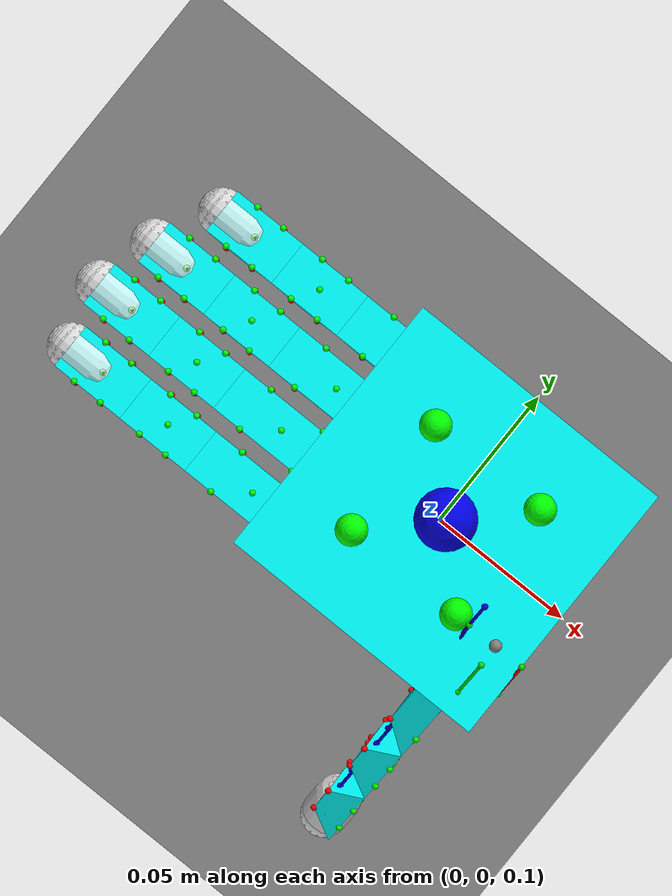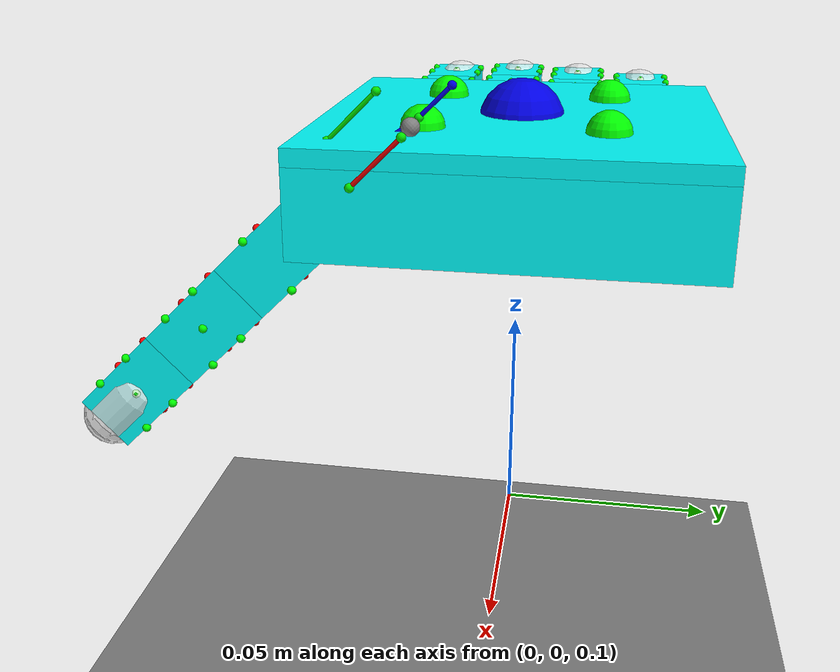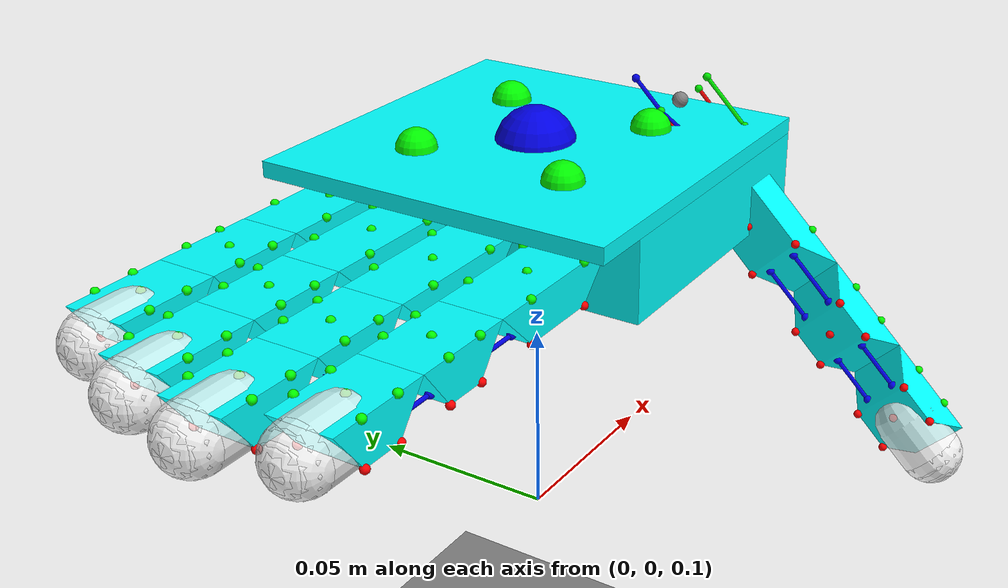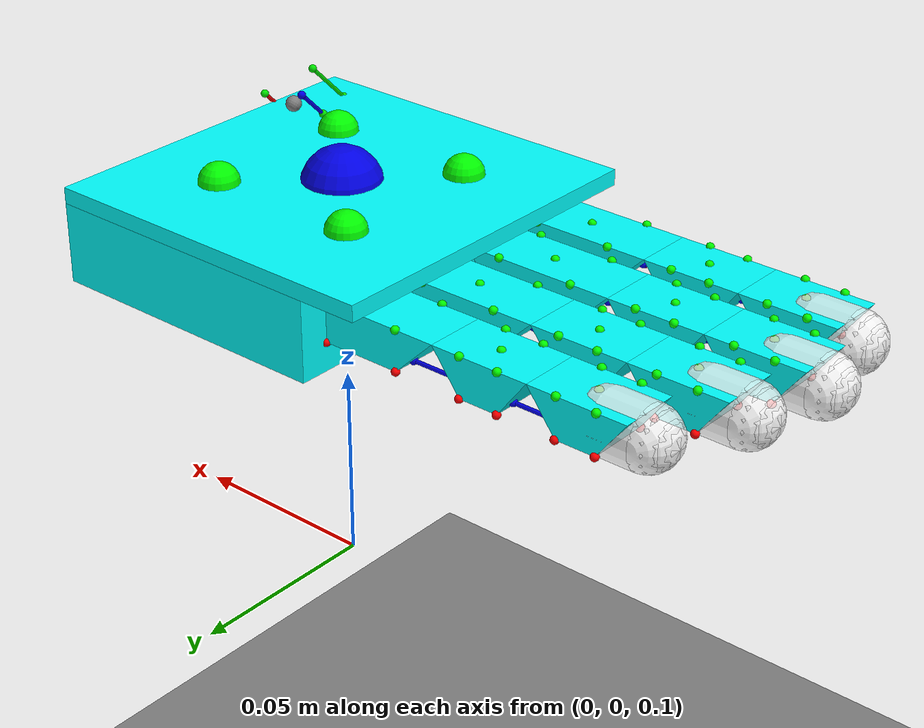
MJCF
<mujoco model="hand">
    <compiler angle="radian" />

    <option integrator="implicitfast"/>

    <!-- TODO： Too large njmax and nconmax may cause problems -->
    <size njmax="5000" nconmax="10000" />

        <visual>
        <global offwidth="1280" offheight="720"/>
    </visual>
    <asset>
        <mesh name="thumb_base_link" vertex="0.0 0.0 -0.0075 0.04 0.0 -0.0075 0.03 0.01 -0.0075 0.01 0.01 -0.0075 0.0 0.0 0.0075 0.04 0.0 0.0075 0.03 0.01 0.0075 0.01 0.01 0.0075" normal="-0.7734590803390136 -0.3203772410170408 -0.5469181606780271 0.7734590803390136 -0.3203772410170408 -0.5469181606780271 0.2971085791188998 0.7172835612062476 -0.6302624731310217 -0.29710857911889976 0.7172835612062476 -0.6302624731310217 -0.7734590803390136 -0.32037724101704074 0.5469181606780271 0.7734590803390138 -0.32037724101704057 0.5469181606780271 0.29710857911889976 0.7172835612062477 0.6302624731310216 -0.29710857911889976 0.7172835612062476 0.6302624731310217" face="1 0 3 3 2 1 7 4 5 5 6 7 5 4 1 1 4 0 6 5 2 2 5 1 4 7 0 0 7 3 7 6 3 3 6 2"/>
        <mesh name="thumb_link_1" vertex="0.0 0.0 -0.0075 0.04 0.0 -0.0075 0.03 0.01 -0.0075 0.01 0.01 -0.0075 0.0 0.0 0.0075 0.04 0.0 0.0075 0.03 0.01 0.0075 0.01 0.01 0.0075" normal="-0.7734590803390136 -0.3203772410170408 -0.5469181606780271 0.7734590803390136 -0.3203772410170408 -0.5469181606780271 0.2971085791188998 0.7172835612062476 -0.6302624731310217 -0.29710857911889976 0.7172835612062476 -0.6302624731310217 -0.7734590803390136 -0.32037724101704074 0.5469181606780271 0.7734590803390138 -0.32037724101704057 0.5469181606780271 0.29710857911889976 0.7172835612062477 0.6302624731310216 -0.29710857911889976 0.7172835612062476 0.6302624731310217" face="1 0 3 3 2 1 7 4 5 5 6 7 5 4 1 1 4 0 6 5 2 2 5 1 4 7 0 0 7 3 7 6 3 3 6 2" />
        <mesh name="thumb_link_2" vertex="0.0 0.0 -0.0075 0.025 0.0 -0.0075 0.0175 0.01 -0.0075 0.007500000000000001 0.01 -0.0075 0.0 0.0 0.0075 0.025 0.0 0.0075 0.0175 0.01 0.0075 0.007500000000000001 0.01 0.0075" normal="-0.7464925414001442 -0.3732462707000721 -0.5508503490444955 0.7464925414001442 -0.3732462707000721 -0.5508503490444956 0.351257248032334 0.702514496064668 -0.618944043128098 -0.351257248032334 0.702514496064668 -0.618944043128098 -0.7464925414001442 -0.3732462707000721 0.5508503490444955 0.7464925414001442 -0.373246270700072 0.5508503490444956 0.351257248032334 0.7025144960646681 0.618944043128098 -0.351257248032334 0.702514496064668 0.618944043128098" face="1 0 3 3 2 1 7 4 5 5 6 7 5 4 1 1 4 0 6 5 2 2 5 1 4 7 0 0 7 3 7 6 3 3 6 2" />
        <mesh name="thumb_link_3" vertex="0.0 0.0 -0.0075 0.025 0.0 -0.0075 0.0175 0.01 -0.0075 0.007500000000000001 0.01 -0.0075 0.0 0.0 0.0075 0.025 0.0 0.0075 0.0175 0.01 0.0075 0.007500000000000001 0.01 0.0075" normal="-0.7464925414001442 -0.3732462707000721 -0.5508503490444955 0.7464925414001442 -0.3732462707000721 -0.5508503490444956 0.351257248032334 0.702514496064668 -0.618944043128098 -0.351257248032334 0.702514496064668 -0.618944043128098 -0.7464925414001442 -0.3732462707000721 0.5508503490444955 0.7464925414001442 -0.373246270700072 0.5508503490444956 0.351257248032334 0.7025144960646681 0.618944043128098 -0.351257248032334 0.702514496064668 0.618944043128098" face="1 0 3 3 2 1 7 4 5 5 6 7 5 4 1 1 4 0 6 5 2 2 5 1 4 7 0 0 7 3 7 6 3 3 6 2" />

        <mesh name="index_base_link" vertex="0.0 0.0 -0.0075 0.04 0.0 -0.0075 0.03 0.01 -0.0075 0.01 0.01 -0.0075 0.0 0.0 0.0075 0.04 0.0 0.0075 0.03 0.01 0.0075 0.01 0.01 0.0075" normal="-0.7734590803390136 -0.3203772410170408 -0.5469181606780271 0.7734590803390136 -0.3203772410170408 -0.5469181606780271 0.2971085791188998 0.7172835612062476 -0.6302624731310217 -0.29710857911889976 0.7172835612062476 -0.6302624731310217 -0.7734590803390136 -0.32037724101704074 0.5469181606780271 0.7734590803390138 -0.32037724101704057 0.5469181606780271 0.29710857911889976 0.7172835612062477 0.6302624731310216 -0.29710857911889976 0.7172835612062476 0.6302624731310217" face="1 0 3 3 2 1 7 4 5 5 6 7 5 4 1 1 4 0 6 5 2 2 5 1 4 7 0 0 7 3 7 6 3 3 6 2"/>
        <mesh name="index_link_1" vertex="0.0 0.0 -0.0075 0.04 0.0 -0.0075 0.03 0.01 -0.0075 0.01 0.01 -0.0075 0.0 0.0 0.0075 0.04 0.0 0.0075 0.03 0.01 0.0075 0.01 0.01 0.0075" normal="-0.7734590803390136 -0.3203772410170408 -0.5469181606780271 0.7734590803390136 -0.3203772410170408 -0.5469181606780271 0.2971085791188998 0.7172835612062476 -0.6302624731310217 -0.29710857911889976 0.7172835612062476 -0.6302624731310217 -0.7734590803390136 -0.32037724101704074 0.5469181606780271 0.7734590803390138 -0.32037724101704057 0.5469181606780271 0.29710857911889976 0.7172835612062477 0.6302624731310216 -0.29710857911889976 0.7172835612062476 0.6302624731310217" face="1 0 3 3 2 1 7 4 5 5 6 7 5 4 1 1 4 0 6 5 2 2 5 1 4 7 0 0 7 3 7 6 3 3 6 2" />
        <mesh name="index_link_2" vertex="0.0 0.0 -0.0075 0.025 0.0 -0.0075 0.0175 0.01 -0.0075 0.007500000000000001 0.01 -0.0075 0.0 0.0 0.0075 0.025 0.0 0.0075 0.0175 0.01 0.0075 0.007500000000000001 0.01 0.0075" normal="-0.7464925414001442 -0.3732462707000721 -0.5508503490444955 0.7464925414001442 -0.3732462707000721 -0.5508503490444956 0.351257248032334 0.702514496064668 -0.618944043128098 -0.351257248032334 0.702514496064668 -0.618944043128098 -0.7464925414001442 -0.3732462707000721 0.5508503490444955 0.7464925414001442 -0.373246270700072 0.5508503490444956 0.351257248032334 0.7025144960646681 0.618944043128098 -0.351257248032334 0.702514496064668 0.618944043128098" face="1 0 3 3 2 1 7 4 5 5 6 7 5 4 1 1 4 0 6 5 2 2 5 1 4 7 0 0 7 3 7 6 3 3 6 2" />
        <mesh name="index_link_3" vertex="0.0 0.0 -0.0075 0.025 0.0 -0.0075 0.0175 0.01 -0.0075 0.007500000000000001 0.01 -0.0075 0.0 0.0 0.0075 0.025 0.0 0.0075 0.0175 0.01 0.0075 0.007500000000000001 0.01 0.0075" normal="-0.7464925414001442 -0.3732462707000721 -0.5508503490444955 0.7464925414001442 -0.3732462707000721 -0.5508503490444956 0.351257248032334 0.702514496064668 -0.618944043128098 -0.351257248032334 0.702514496064668 -0.618944043128098 -0.7464925414001442 -0.3732462707000721 0.5508503490444955 0.7464925414001442 -0.373246270700072 0.5508503490444956 0.351257248032334 0.7025144960646681 0.618944043128098 -0.351257248032334 0.702514496064668 0.618944043128098" face="1 0 3 3 2 1 7 4 5 5 6 7 5 4 1 1 4 0 6 5 2 2 5 1 4 7 0 0 7 3 7 6 3 3 6 2" />

        <mesh name="middle_base_link" vertex="0.0 0.0 -0.0075 0.04 0.0 -0.0075 0.03 0.01 -0.0075 0.01 0.01 -0.0075 0.0 0.0 0.0075 0.04 0.0 0.0075 0.03 0.01 0.0075 0.01 0.01 0.0075" normal="-0.7734590803390136 -0.3203772410170408 -0.5469181606780271 0.7734590803390136 -0.3203772410170408 -0.5469181606780271 0.2971085791188998 0.7172835612062476 -0.6302624731310217 -0.29710857911889976 0.7172835612062476 -0.6302624731310217 -0.7734590803390136 -0.32037724101704074 0.5469181606780271 0.7734590803390138 -0.32037724101704057 0.5469181606780271 0.29710857911889976 0.7172835612062477 0.6302624731310216 -0.29710857911889976 0.7172835612062476 0.6302624731310217" face="1 0 3 3 2 1 7 4 5 5 6 7 5 4 1 1 4 0 6 5 2 2 5 1 4 7 0 0 7 3 7 6 3 3 6 2"/>
        <mesh name="middle_link_1" vertex="0.0 0.0 -0.0075 0.04 0.0 -0.0075 0.03 0.01 -0.0075 0.01 0.01 -0.0075 0.0 0.0 0.0075 0.04 0.0 0.0075 0.03 0.01 0.0075 0.01 0.01 0.0075" normal="-0.7734590803390136 -0.3203772410170408 -0.5469181606780271 0.7734590803390136 -0.3203772410170408 -0.5469181606780271 0.2971085791188998 0.7172835612062476 -0.6302624731310217 -0.29710857911889976 0.7172835612062476 -0.6302624731310217 -0.7734590803390136 -0.32037724101704074 0.5469181606780271 0.7734590803390138 -0.32037724101704057 0.5469181606780271 0.29710857911889976 0.7172835612062477 0.6302624731310216 -0.29710857911889976 0.7172835612062476 0.6302624731310217" face="1 0 3 3 2 1 7 4 5 5 6 7 5 4 1 1 4 0 6 5 2 2 5 1 4 7 0 0 7 3 7 6 3 3 6 2" />
        <mesh name="middle_link_2" vertex="0.0 0.0 -0.0075 0.025 0.0 -0.0075 0.0175 0.01 -0.0075 0.007500000000000001 0.01 -0.0075 0.0 0.0 0.0075 0.025 0.0 0.0075 0.0175 0.01 0.0075 0.007500000000000001 0.01 0.0075" normal="-0.7464925414001442 -0.3732462707000721 -0.5508503490444955 0.7464925414001442 -0.3732462707000721 -0.5508503490444956 0.351257248032334 0.702514496064668 -0.618944043128098 -0.351257248032334 0.702514496064668 -0.618944043128098 -0.7464925414001442 -0.3732462707000721 0.5508503490444955 0.7464925414001442 -0.373246270700072 0.5508503490444956 0.351257248032334 0.7025144960646681 0.618944043128098 -0.351257248032334 0.702514496064668 0.618944043128098" face="1 0 3 3 2 1 7 4 5 5 6 7 5 4 1 1 4 0 6 5 2 2 5 1 4 7 0 0 7 3 7 6 3 3 6 2" />
        <mesh name="middle_link_3" vertex="0.0 0.0 -0.0075 0.025 0.0 -0.0075 0.0175 0.01 -0.0075 0.007500000000000001 0.01 -0.0075 0.0 0.0 0.0075 0.025 0.0 0.0075 0.0175 0.01 0.0075 0.007500000000000001 0.01 0.0075" normal="-0.7464925414001442 -0.3732462707000721 -0.5508503490444955 0.7464925414001442 -0.3732462707000721 -0.5508503490444956 0.351257248032334 0.702514496064668 -0.618944043128098 -0.351257248032334 0.702514496064668 -0.618944043128098 -0.7464925414001442 -0.3732462707000721 0.5508503490444955 0.7464925414001442 -0.373246270700072 0.5508503490444956 0.351257248032334 0.7025144960646681 0.618944043128098 -0.351257248032334 0.702514496064668 0.618944043128098" face="1 0 3 3 2 1 7 4 5 5 6 7 5 4 1 1 4 0 6 5 2 2 5 1 4 7 0 0 7 3 7 6 3 3 6 2" />

        <mesh name="ring_base_link" vertex="0.0 0.0 -0.0075 0.04 0.0 -0.0075 0.03 0.01 -0.0075 0.01 0.01 -0.0075 0.0 0.0 0.0075 0.04 0.0 0.0075 0.03 0.01 0.0075 0.01 0.01 0.0075" normal="-0.7734590803390136 -0.3203772410170408 -0.5469181606780271 0.7734590803390136 -0.3203772410170408 -0.5469181606780271 0.2971085791188998 0.7172835612062476 -0.6302624731310217 -0.29710857911889976 0.7172835612062476 -0.6302624731310217 -0.7734590803390136 -0.32037724101704074 0.5469181606780271 0.7734590803390138 -0.32037724101704057 0.5469181606780271 0.29710857911889976 0.7172835612062477 0.6302624731310216 -0.29710857911889976 0.7172835612062476 0.6302624731310217" face="1 0 3 3 2 1 7 4 5 5 6 7 5 4 1 1 4 0 6 5 2 2 5 1 4 7 0 0 7 3 7 6 3 3 6 2"/>
        <mesh name="ring_link_1" vertex="0.0 0.0 -0.0075 0.04 0.0 -0.0075 0.03 0.01 -0.0075 0.01 0.01 -0.0075 0.0 0.0 0.0075 0.04 0.0 0.0075 0.03 0.01 0.0075 0.01 0.01 0.0075" normal="-0.7734590803390136 -0.3203772410170408 -0.5469181606780271 0.7734590803390136 -0.3203772410170408 -0.5469181606780271 0.2971085791188998 0.7172835612062476 -0.6302624731310217 -0.29710857911889976 0.7172835612062476 -0.6302624731310217 -0.7734590803390136 -0.32037724101704074 0.5469181606780271 0.7734590803390138 -0.32037724101704057 0.5469181606780271 0.29710857911889976 0.7172835612062477 0.6302624731310216 -0.29710857911889976 0.7172835612062476 0.6302624731310217" face="1 0 3 3 2 1 7 4 5 5 6 7 5 4 1 1 4 0 6 5 2 2 5 1 4 7 0 0 7 3 7 6 3 3 6 2" />
        <mesh name="ring_link_2" vertex="0.0 0.0 -0.0075 0.025 0.0 -0.0075 0.0175 0.01 -0.0075 0.007500000000000001 0.01 -0.0075 0.0 0.0 0.0075 0.025 0.0 0.0075 0.0175 0.01 0.0075 0.007500000000000001 0.01 0.0075" normal="-0.7464925414001442 -0.3732462707000721 -0.5508503490444955 0.7464925414001442 -0.3732462707000721 -0.5508503490444956 0.351257248032334 0.702514496064668 -0.618944043128098 -0.351257248032334 0.702514496064668 -0.618944043128098 -0.7464925414001442 -0.3732462707000721 0.5508503490444955 0.7464925414001442 -0.373246270700072 0.5508503490444956 0.351257248032334 0.7025144960646681 0.618944043128098 -0.351257248032334 0.702514496064668 0.618944043128098" face="1 0 3 3 2 1 7 4 5 5 6 7 5 4 1 1 4 0 6 5 2 2 5 1 4 7 0 0 7 3 7 6 3 3 6 2" />
        <mesh name="ring_link_3" vertex="0.0 0.0 -0.0075 0.025 0.0 -0.0075 0.0175 0.01 -0.0075 0.007500000000000001 0.01 -0.0075 0.0 0.0 0.0075 0.025 0.0 0.0075 0.0175 0.01 0.0075 0.007500000000000001 0.01 0.0075" normal="-0.7464925414001442 -0.3732462707000721 -0.5508503490444955 0.7464925414001442 -0.3732462707000721 -0.5508503490444956 0.351257248032334 0.702514496064668 -0.618944043128098 -0.351257248032334 0.702514496064668 -0.618944043128098 -0.7464925414001442 -0.3732462707000721 0.5508503490444955 0.7464925414001442 -0.373246270700072 0.5508503490444956 0.351257248032334 0.7025144960646681 0.618944043128098 -0.351257248032334 0.702514496064668 0.618944043128098" face="1 0 3 3 2 1 7 4 5 5 6 7 5 4 1 1 4 0 6 5 2 2 5 1 4 7 0 0 7 3 7 6 3 3 6 2" />

        <mesh name="little_base_link" vertex="0.0 0.0 -0.0075 0.04 0.0 -0.0075 0.03 0.01 -0.0075 0.01 0.01 -0.0075 0.0 0.0 0.0075 0.04 0.0 0.0075 0.03 0.01 0.0075 0.01 0.01 0.0075" normal="-0.7734590803390136 -0.3203772410170408 -0.5469181606780271 0.7734590803390136 -0.3203772410170408 -0.5469181606780271 0.2971085791188998 0.7172835612062476 -0.6302624731310217 -0.29710857911889976 0.7172835612062476 -0.6302624731310217 -0.7734590803390136 -0.32037724101704074 0.5469181606780271 0.7734590803390138 -0.32037724101704057 0.5469181606780271 0.29710857911889976 0.7172835612062477 0.6302624731310216 -0.29710857911889976 0.7172835612062476 0.6302624731310217" face="1 0 3 3 2 1 7 4 5 5 6 7 5 4 1 1 4 0 6 5 2 2 5 1 4 7 0 0 7 3 7 6 3 3 6 2"/>
        <mesh name="little_link_1" vertex="0.0 0.0 -0.0075 0.04 0.0 -0.0075 0.03 0.01 -0.0075 0.01 0.01 -0.0075 0.0 0.0 0.0075 0.04 0.0 0.0075 0.03 0.01 0.0075 0.01 0.01 0.0075" normal="-0.7734590803390136 -0.3203772410170408 -0.5469181606780271 0.7734590803390136 -0.3203772410170408 -0.5469181606780271 0.2971085791188998 0.7172835612062476 -0.6302624731310217 -0.29710857911889976 0.7172835612062476 -0.6302624731310217 -0.7734590803390136 -0.32037724101704074 0.5469181606780271 0.7734590803390138 -0.32037724101704057 0.5469181606780271 0.29710857911889976 0.7172835612062477 0.6302624731310216 -0.29710857911889976 0.7172835612062476 0.6302624731310217" face="1 0 3 3 2 1 7 4 5 5 6 7 5 4 1 1 4 0 6 5 2 2 5 1 4 7 0 0 7 3 7 6 3 3 6 2" />
        <mesh name="little_link_2" vertex="0.0 0.0 -0.0075 0.025 0.0 -0.0075 0.0175 0.01 -0.0075 0.007500000000000001 0.01 -0.0075 0.0 0.0 0.0075 0.025 0.0 0.0075 0.0175 0.01 0.0075 0.007500000000000001 0.01 0.0075" normal="-0.7464925414001442 -0.3732462707000721 -0.5508503490444955 0.7464925414001442 -0.3732462707000721 -0.5508503490444956 0.351257248032334 0.702514496064668 -0.618944043128098 -0.351257248032334 0.702514496064668 -0.618944043128098 -0.7464925414001442 -0.3732462707000721 0.5508503490444955 0.7464925414001442 -0.373246270700072 0.5508503490444956 0.351257248032334 0.7025144960646681 0.618944043128098 -0.351257248032334 0.702514496064668 0.618944043128098" face="1 0 3 3 2 1 7 4 5 5 6 7 5 4 1 1 4 0 6 5 2 2 5 1 4 7 0 0 7 3 7 6 3 3 6 2" />
        <mesh name="little_link_3" vertex="0.0 0.0 -0.0075 0.025 0.0 -0.0075 0.0175 0.01 -0.0075 0.007500000000000001 0.01 -0.0075 0.0 0.0 0.0075 0.025 0.0 0.0075 0.0175 0.01 0.0075 0.007500000000000001 0.01 0.0075" normal="-0.7464925414001442 -0.3732462707000721 -0.5508503490444955 0.7464925414001442 -0.3732462707000721 -0.5508503490444956 0.351257248032334 0.702514496064668 -0.618944043128098 -0.351257248032334 0.702514496064668 -0.618944043128098 -0.7464925414001442 -0.3732462707000721 0.5508503490444955 0.7464925414001442 -0.373246270700072 0.5508503490444956 0.351257248032334 0.7025144960646681 0.618944043128098 -0.351257248032334 0.702514496064668 0.618944043128098" face="1 0 3 3 2 1 7 4 5 5 6 7 5 4 1 1 4 0 6 5 2 2 5 1 4 7 0 0 7 3 7 6 3 3 6 2" />

        <texture type="2d" name="groundplane" builtin="checker" mark="edge" rgb1="1 1 1" rgb2="0 0 0" markrgb="0 0 0" width="300" height="300"/>
        <material name="groundplane" texture="groundplane" texuniform="true" texrepeat="5 5" reflectance="0"/>
    </asset>
    <option gravity="0 0 -9.8"/>

    <default>
        <geom solref="0.001 1" solimp="0.99 0.999 0.0001"/>
    </default>

    <option>
        <flag filterparent ="disable"/>
    </option>
    <contact>
        <exclude body1="palm" body2="thumb_link_1"/>
        <exclude body1="palm" body2="index_link_1"/>
        <exclude body1="palm" body2="middle_link_1"/>
        <exclude body1="palm" body2="ring_link_1"/>
        <exclude body1="palm" body2="little_link_1"/>
    </contact>
    <worldbody>
    <geom name="floor" pos="0 0 0" size="0 0 0.01" type="plane" material="groundplane" contype="1" conaffinity="1" friction="1 0.05 0.05" solref="0.001 1" solimp="0.98 0.99 0.001"/>
    <site name="target" size="0.01" rgba="0 0 .9 1" pos="0 0 .2"/>
    <body name="palm" pos="0 0 0.2" euler="0 3.14 0">
        <joint name="palm_slide_x" type="slide" axis="1 0 0" range="-.5 .5" limited="true" solreflimit=".001 1" solimplimit="0.97 0.99 0.00001 0.1 2" damping="0.2"/>
        <joint name="palm_slide_y" type="slide" axis="0 1 0" range="-.5 .5" limited="true" solreflimit=".001 1" solimplimit="0.97 0.99 0.00001 0.1 2" damping="0.2"/>
        <joint name="palm_slide_z" type="slide" axis="0 0 1" range="-.2 .12" limited="true" solreflimit=".001 1" solimplimit="0.97 0.99 0.00001 0.1 2" damping="0.2"/>
        <joint name="palm_rotate_x" type="hinge" axis="1 0 0" range="-1.57 1.57" limited="true" solreflimit=".001 1" solimplimit="0.97 0.99 0.00001 0.1 2" damping="0.2"/>
        <joint name="palm_rotate_y" type="hinge" axis="0 1 0" range="-1.57 1.57" limited="true" solreflimit=".001 1" solimplimit="0.97 0.99 0.00001 0.1 2" damping="0.2"/>
        <joint name="palm_rotate_z" type="hinge" axis="0 0 1" range="-3.14 3.14" limited="true" solreflimit=".001 1" solimplimit="0.97 0.99 0.00001 0.1 2" damping="0.2"/>
        <geom type="box" size="0.045 0.045 0.002" rgba="0 1 1 1" density="200"/>
        <geom type="box" size="0.0375 0.045 0.01" pos="-0.0075 0 0.012" rgba="0 1 1 1" density="200"/>
        <site name="inner_palm_1" size="0.005" rgba="1 0 0 1" pos=".02 .02 0.022"/>
        <site name="inner_palm_2" size="0.005" rgba="1 0 0 1" pos=".02 -.02 0.022"/>
        <site name="inner_palm_3" size="0.005" rgba="1 0 0 1" pos="-.02 .02 0.022"/>
        <site name="inner_palm_4" size="0.005" rgba="1 0 0 1" pos="-.02 -.02 0.022"/>
        <site name="outer_palm_1" size="0.005" rgba="0 1 0 1" pos=".02 .02 -0.002"/>
        <site name="outer_palm_2" size="0.005" rgba="0 1 0 1" pos=".02 -.02 -0.002"/>
        <site name="outer_palm_3" size="0.005" rgba="0 1 0 1" pos="-.02 .02 -0.002"/>
        <site name="outer_palm_4" size="0.005" rgba="0 1 0 1" pos="-.02 -.02 -0.002"/>

                <body name="thumb_base_link" pos="-0.035 -0.02 -0.005" euler="-0.785 0 -1.57">
                    <geom conaffinity="0" contype="0" type="sphere" size=".002"/>
                    <site name="thumb_ty_1_1" pos="0 0 0.01" size="0.001" rgba="0 0.9 0 1"/>
            <site name="thumb_ty_2_1" pos="0 0 -0.01" size="0.001" rgba="0 0.9 0 1"/>
            <site name="thumb_tx_1_1" pos="0 0.01 0" size="0.001" rgba="0 0.9 0 1"/>
            <site name="thumb_tx_2_1" pos="0 -0.01 0" size="0.001" rgba="0 0.9 0 1"/>
            <site name="thumb_t12" pos="0 0.01 0" size="0.001" rgba="0 0 0.9 1"/>
            <site name="thumb_t0" pos="-0.01 0.01 0" size="0.001" rgba="0 0 0.9 1"/>

                    <body name="thumb_link_1" pos="0.015 0 0">
                        <joint name="thumb_universal_1"
                            pos="0 0 0"
                            axis="0 0 1"
                            damping="0.1"/>
                        <joint name="thumb_universal_2"
                            pos="0 0 0"
                            axis="0 1 0"
                            damping="0.1"/>

            <geom type="box" pos="0.02 0.005 0" size="0.01 0.005 0.0075" name="thumb_link_1_box_center"
        density="200"
         rgba="0 0 1 0"/>
            <geom type="box" pos="0.03358578654972743 0.004999436911938167 0" size="0.0060674574081405145 0.001 0.0075" euler="0 0 -0.785" name="thumb_link_1_box_slope1"
        density="200"
         rgba="0 0 1 0"/>
            <geom type="box" pos="0.006414213450272566 0.005000563088061833 0" size="0.0060674574081405145 0.001 0.0075" euler="0 0 0.785" name="thumb_link_1_box_slope2"
        density="200"
         rgba="0 0 1 0"/>
            <geom type="box" pos="0.02 0.001 0" size="0.018000000000000002 0.001 0.0075" euler="0 0 0" name="thumb_link_1_box_bottom"
        density="200"
         rgba="0 0 1 0"/>
            <site name="inner_thumb_1_0" size="0.001" rgba="1 0 0 1" pos="0.02 0.01 0"/>
            <site name="inner_thumb_1_1" size="0.001" rgba="1 0 0 1" pos="0.01 0.01 0.0075"/>
            <site name="inner_thumb_1_2" size="0.001" rgba="1 0 0 1" pos="0.01 0.01 -0.0075"/>
            <site name="inner_thumb_1_3" size="0.001" rgba="1 0 0 1" pos="0.03 0.01 0.0075"/>
            <site name="inner_thumb_1_4" size="0.001" rgba="1 0 0 1" pos="0.03 0.01 -0.0075"/>
            <site name="outer_thumb_1_0" size="0.001" rgba="0 1 0 1" pos="0.02 0 0"/>
            <site name="outer_thumb_1_1" size="0.001" rgba="0 1 0 1" pos="0.01 0 0.0075"/>
            <site name="outer_thumb_1_2" size="0.001" rgba="0 1 0 1" pos="0.01 0 -0.0075"/>
            <site name="outer_thumb_1_3" size="0.001" rgba="0 1 0 1" pos="0.03 0 0.0075"/>
            <site name="outer_thumb_1_4" size="0.001" rgba="0 1 0 1" pos="0.03 0 -0.0075"/>

                        <geom conaffinity="0" contype="0" type="mesh" rgba="0 1 1 1" mesh="thumb_link_1"/>
                    <site name="thumb_ty_1_2" pos="0 0 0.01" size="0.001" rgba="0 0.9 0 1"/>
            <site name="thumb_ty_2_2" pos="0 0 -0.01" size="0.001" rgba="0 0.9 0 1"/>
            <site name="thumb_tx_1_2" pos="0 0.01 0" size="0.001" rgba="0 0.9 0 1"/>
            <site name="thumb_tx_2_2" pos="0 -0.01 0" size="0.001" rgba="0 0.9 0 1"/>
            <site name="thumb_t1_1_1" pos="0.008 0.008 0.004" size="0.001" rgba="0 0 0.9 1"/>
            <site name="thumb_t2_1_1" pos="0.008 0.008 -0.004" size="0.001" rgba="0 0 0.9 1"/>
            <site name="thumb_t1_1_2" pos="0.032 0.008 0.004" size="0.001" rgba="0 0 0.9 1"/>
            <site name="thumb_t2_1_2" pos="0.032 0.008 -0.004" size="0.001" rgba="0 0 0.9 1"/>

                        <body name="thumb_link_2" pos="0.04 0 0">
                            <joint name="thumb_joint_1"
                                pos="0 0 0"
                                axis="0 0 1"
                                stiffness="0.1"
                                springref="0.0"
                                damping="0.2"
                                range="0 1.3"
        limited="true" solreflimit=".001 1" solimplimit="0.97 0.99 0.00001 0.1 2"
        />

            <geom type="box" pos="0.0125 0.005 0" size="0.005 0.005 0.0075" name="thumb_link_2_box_center"
        density="200"
         rgba="0 0 1 0"/>
            <geom type="box" pos="0.019849544644419077 0.005196786170816701 0" size="0.005477355448802637 0.001 0.0075" euler="0 0 -0.925" name="thumb_link_2_box_slope1"
        density="200"
         rgba="0 0 1 0"/>
            <geom type="box" pos="0.0051504553555809275 0.004803213829183299 0" size="0.005477355448802637 0.001 0.0075" euler="0 0 0.925" name="thumb_link_2_box_slope2"
        density="200"
         rgba="0 0 1 0"/>
            <geom type="box" pos="0.0125 0.001 0" size="0.0105 0.001 0.0075" euler="0 0 0" name="thumb_link_2_box_bottom"
        density="200"
         rgba="0 0 1 0"/>
            <site name="inner_thumb_2_0" size="0.001" rgba="1 0 0 1" pos="0.0125 0.01 0"/>
            <site name="inner_thumb_2_1" size="0.001" rgba="1 0 0 1" pos="0.007500000000000001 0.01 0.0075"/>
            <site name="inner_thumb_2_2" size="0.001" rgba="1 0 0 1" pos="0.007500000000000001 0.01 -0.0075"/>
            <site name="inner_thumb_2_3" size="0.001" rgba="1 0 0 1" pos="0.0175 0.01 0.0075"/>
            <site name="inner_thumb_2_4" size="0.001" rgba="1 0 0 1" pos="0.0175 0.01 -0.0075"/>
            <site name="outer_thumb_2_0" size="0.001" rgba="0 1 0 1" pos="0.0125 0 0"/>
            <site name="outer_thumb_2_1" size="0.001" rgba="0 1 0 1" pos="0.007500000000000001 0 0.0075"/>
            <site name="outer_thumb_2_2" size="0.001" rgba="0 1 0 1" pos="0.007500000000000001 0 -0.0075"/>
            <site name="outer_thumb_2_3" size="0.001" rgba="0 1 0 1" pos="0.0175 0 0.0075"/>
            <site name="outer_thumb_2_4" size="0.001" rgba="0 1 0 1" pos="0.0175 0 -0.0075"/>

                            <geom conaffinity="0" contype="0" type="mesh" rgba="0 1 1 1" mesh="thumb_link_2"/>
                    <site name="thumb_t1_2_1" pos="0.006 0.008 0.004" size="0.001" rgba="0 0 0.9 1"/>
            <site name="thumb_t2_2_1" pos="0.006 0.008 -0.004" size="0.001" rgba="0 0 0.9 1"/>
            <site name="thumb_t1_2_2" pos="0.019000000000000003 0.008 0.004" size="0.001" rgba="0 0 0.9 1"/>
            <site name="thumb_t2_2_2" pos="0.019000000000000003 0.008 -0.004" size="0.001" rgba="0 0 0.9 1"/>

                            <body name="thumb_link_3" pos="0.025 0 0">
                                <joint name="thumb_joint_2"
                                    pos="0 0 0"
                                    axis="0 0 1"
                                    stiffness="0.1"
                                    springref="0.0"
                                    damping="0.2"
                                    range="0 1.3"
        limited="true" solreflimit=".001 1" solimplimit="0.97 0.99 0.00001 0.1 2"
        />

            <geom type="box" pos="0.0125 0.005 0" size="0.005 0.005 0.0075" name="thumb_link_3_box_center"
        density="200"
         rgba="0 0 1 0"/>

            <geom type="box" pos="0.0051504553555809275 0.004803213829183299 0" size="0.005477355448802637 0.001 0.0075" euler="0 0 0.925" name="thumb_link_3_box_slope2"
        density="200"
         rgba="0 0 1 0"/>
            <site name="inner_thumb_3_0" size="0.001" rgba="1 0 0 1" pos="0.0125 0.01 0"/>
            <site name="inner_thumb_3_1" size="0.001" rgba="1 0 0 1" pos="0.007500000000000001 0.01 0.0075"/>
            <site name="inner_thumb_3_2" size="0.001" rgba="1 0 0 1" pos="0.007500000000000001 0.01 -0.0075"/>
            <site name="inner_thumb_3_3" size="0.001" rgba="1 0 0 1" pos="0.0175 0.01 0.0075"/>
            <site name="inner_thumb_3_4" size="0.001" rgba="1 0 0 1" pos="0.0175 0.01 -0.0075"/>
            <site name="outer_thumb_3_0" size="0.001" rgba="0 1 0 1" pos="0.0125 0 0"/>
            <site name="outer_thumb_3_1" size="0.001" rgba="0 1 0 1" pos="0.007500000000000001 0 0.0075"/>
            <site name="outer_thumb_3_2" size="0.001" rgba="0 1 0 1" pos="0.007500000000000001 0 -0.0075"/>
            <site name="outer_thumb_3_3" size="0.001" rgba="0 1 0 1" pos="0.0175 0 0.0075"/>
            <site name="outer_thumb_3_4" size="0.001" rgba="0 1 0 1" pos="0.0175 0 -0.0075"/>
            <geom type="sphere" pos="0.025 0.006 0" size="0.0075" rgba="1 1 1 .8"
        density="200" friction="5 0.5 0.05"
        />
            <geom type="capsule" euler="0 1.57 0" pos="0.02 0.006 0" size="0.0075 0.005000000000000001" rgba="1 1 1 .8"
        density="200" friction="5 0.5 0.05"
        />

                                <geom conaffinity="0" contype="0" type="mesh" rgba="0 1 1 1" mesh="thumb_link_3"/>
                    <site name="thumb_t1_3" pos="0.006 0.008 0.004" size="0.001" rgba="0 0 0.9 1"/>
            <site name="thumb_t2_3" pos="0.006 0.008 -0.004" size="0.001" rgba="0 0 0.9 1"/>
                                <body name="thumb_fingertip" pos="0.02 0.01 0 " euler="1.57 0 0">
                                    <geom conaffinity="0" contype="0" type="sphere" pos="0 0 0" size=".001" rgba=".9 0 0 .1"/>
                                    <!--这里插入tactile-->

                                </body>
                            </body>
                        </body>
                    </body>
                </body>

                <body name="index_base_link" pos="0.015 -0.03 0.005" euler="1.57 0 0">

                    <joint name="index_swing" axis="0 -1 0" range="0 0.5"
        limited="true" solreflimit=".001 1" solimplimit="0.97 0.99 0.00001 0.1 2"
         damping="0.2"/>

                    <geom conaffinity="0" contype="0" type="sphere" size=".002"/>
                    <site name="index_t12" pos="0 0 0" size="0.001" rgba="0 0 0.9 1"/>
            <site name="index_t0" pos="-0.01 0 0" size="0.001" rgba="0 0 0.9 1"/>

                    <body name="index_link_1" pos="0.015 0 0">
                        <joint name="index_joint_0"
                                pos="0 0 0"
                                axis="0 0 1"
                                stiffness="0.1"
                                springref="0.0"
                                damping="0.2"
                                range="0 0.7"
        limited="true" solreflimit=".001 1" solimplimit="0.97 0.99 0.00001 0.1 2"
        />

            <geom type="box" pos="0.02 0.005 0" size="0.01 0.005 0.0075" name="index_link_1_box_center"
        density="200"
         rgba="0 0 1 0"/>
            <geom type="box" pos="0.03358578654972743 0.004999436911938167 0" size="0.0060674574081405145 0.001 0.0075" euler="0 0 -0.785" name="index_link_1_box_slope1"
        density="200"
         rgba="0 0 1 0"/>
            <geom type="box" pos="0.006414213450272566 0.005000563088061833 0" size="0.0060674574081405145 0.001 0.0075" euler="0 0 0.785" name="index_link_1_box_slope2"
        density="200"
         rgba="0 0 1 0"/>
            <geom type="box" pos="0.02 0.001 0" size="0.018000000000000002 0.001 0.0075" euler="0 0 0" name="index_link_1_box_bottom"
        density="200"
         rgba="0 0 1 0"/>
            <site name="inner_index_1_0" size="0.001" rgba="1 0 0 1" pos="0.02 0.01 0"/>
            <site name="inner_index_1_1" size="0.001" rgba="1 0 0 1" pos="0.01 0.01 0.0075"/>
            <site name="inner_index_1_2" size="0.001" rgba="1 0 0 1" pos="0.01 0.01 -0.0075"/>
            <site name="inner_index_1_3" size="0.001" rgba="1 0 0 1" pos="0.03 0.01 0.0075"/>
            <site name="inner_index_1_4" size="0.001" rgba="1 0 0 1" pos="0.03 0.01 -0.0075"/>
            <site name="outer_index_1_0" size="0.001" rgba="0 1 0 1" pos="0.02 0 0"/>
            <site name="outer_index_1_1" size="0.001" rgba="0 1 0 1" pos="0.01 0 0.0075"/>
            <site name="outer_index_1_2" size="0.001" rgba="0 1 0 1" pos="0.01 0 -0.0075"/>
            <site name="outer_index_1_3" size="0.001" rgba="0 1 0 1" pos="0.03 0 0.0075"/>
            <site name="outer_index_1_4" size="0.001" rgba="0 1 0 1" pos="0.03 0 -0.0075"/>

                        <geom conaffinity="0" contype="0" type="mesh" rgba="0 1 1 1" mesh="index_link_1"/>
                    <site name="index_t1_1_1" pos="0.008 0.008 0.004" size="0.001" rgba="0 0 0.9 1"/>
            <site name="index_t2_1_1" pos="0.008 0.008 -0.004" size="0.001" rgba="0 0 0.9 1"/>
            <site name="index_t1_1_2" pos="0.032 0.008 0.004" size="0.001" rgba="0 0 0.9 1"/>
            <site name="index_t2_1_2" pos="0.032 0.008 -0.004" size="0.001" rgba="0 0 0.9 1"/>

                        <body name="index_link_2" pos="0.04 0 0">
                            <joint name="index_joint_1"
                                pos="0 0 0"
                                axis="0 0 1"
                                stiffness="0.1"
                                springref="0.0"
                                damping="0.2"
                                range="0 1.3"
        limited="true" solreflimit=".001 1" solimplimit="0.97 0.99 0.00001 0.1 2"
        />

            <geom type="box" pos="0.0125 0.005 0" size="0.005 0.005 0.0075" name="index_link_2_box_center"
        density="200"
         rgba="0 0 1 0"/>
            <geom type="box" pos="0.019849544644419077 0.005196786170816701 0" size="0.005477355448802637 0.001 0.0075" euler="0 0 -0.925" name="index_link_2_box_slope1"
        density="200"
         rgba="0 0 1 0"/>
            <geom type="box" pos="0.0051504553555809275 0.004803213829183299 0" size="0.005477355448802637 0.001 0.0075" euler="0 0 0.925" name="index_link_2_box_slope2"
        density="200"
         rgba="0 0 1 0"/>
            <geom type="box" pos="0.0125 0.001 0" size="0.0105 0.001 0.0075" euler="0 0 0" name="index_link_2_box_bottom"
        density="200"
         rgba="0 0 1 0"/>
            <site name="inner_index_2_0" size="0.001" rgba="1 0 0 1" pos="0.0125 0.01 0"/>
            <site name="inner_index_2_1" size="0.001" rgba="1 0 0 1" pos="0.007500000000000001 0.01 0.0075"/>
            <site name="inner_index_2_2" size="0.001" rgba="1 0 0 1" pos="0.007500000000000001 0.01 -0.0075"/>
            <site name="inner_index_2_3" size="0.001" rgba="1 0 0 1" pos="0.0175 0.01 0.0075"/>
            <site name="inner_index_2_4" size="0.001" rgba="1 0 0 1" pos="0.0175 0.01 -0.0075"/>
            <site name="outer_index_2_0" size="0.001" rgba="0 1 0 1" pos="0.0125 0 0"/>
            <site name="outer_index_2_1" size="0.001" rgba="0 1 0 1" pos="0.007500000000000001 0 0.0075"/>
            <site name="outer_index_2_2" size="0.001" rgba="0 1 0 1" pos="0.007500000000000001 0 -0.0075"/>
            <site name="outer_index_2_3" size="0.001" rgba="0 1 0 1" pos="0.0175 0 0.0075"/>
            <site name="outer_index_2_4" size="0.001" rgba="0 1 0 1" pos="0.0175 0 -0.0075"/>

                            <geom conaffinity="0" contype="0" type="mesh" rgba="0 1 1 1" mesh="index_link_2"/>
                    <site name="index_t1_2_1" pos="0.006 0.008 0.004" size="0.001" rgba="0 0 0.9 1"/>
            <site name="index_t2_2_1" pos="0.006 0.008 -0.004" size="0.001" rgba="0 0 0.9 1"/>
            <site name="index_t1_2_2" pos="0.019000000000000003 0.008 0.004" size="0.001" rgba="0 0 0.9 1"/>
            <site name="index_t2_2_2" pos="0.019000000000000003 0.008 -0.004" size="0.001" rgba="0 0 0.9 1"/>

                            <body name="index_link_3" pos="0.025 0 0">
                                <joint name="index_joint_2"
                                    pos="0 0 0"
                                    axis="0 0 1"
                                    stiffness="0.1"
                                    springref="0.0"
                                    damping="0.2"
                                    range="0 1.3"
        limited="true" solreflimit=".001 1" solimplimit="0.97 0.99 0.00001 0.1 2"
        />

            <geom type="box" pos="0.0125 0.005 0" size="0.005 0.005 0.0075" name="index_link_3_box_center"
        density="200"
         rgba="0 0 1 0"/>

            <geom type="box" pos="0.0051504553555809275 0.004803213829183299 0" size="0.005477355448802637 0.001 0.0075" euler="0 0 0.925" name="index_link_3_box_slope2"
        density="200"
         rgba="0 0 1 0"/>
            <site name="inner_index_3_0" size="0.001" rgba="1 0 0 1" pos="0.0125 0.01 0"/>
            <site name="inner_index_3_1" size="0.001" rgba="1 0 0 1" pos="0.007500000000000001 0.01 0.0075"/>
            <site name="inner_index_3_2" size="0.001" rgba="1 0 0 1" pos="0.007500000000000001 0.01 -0.0075"/>
            <site name="inner_index_3_3" size="0.001" rgba="1 0 0 1" pos="0.0175 0.01 0.0075"/>
            <site name="inner_index_3_4" size="0.001" rgba="1 0 0 1" pos="0.0175 0.01 -0.0075"/>
            <site name="outer_index_3_0" size="0.001" rgba="0 1 0 1" pos="0.0125 0 0"/>
            <site name="outer_index_3_1" size="0.001" rgba="0 1 0 1" pos="0.007500000000000001 0 0.0075"/>
            <site name="outer_index_3_2" size="0.001" rgba="0 1 0 1" pos="0.007500000000000001 0 -0.0075"/>
            <site name="outer_index_3_3" size="0.001" rgba="0 1 0 1" pos="0.0175 0 0.0075"/>
            <site name="outer_index_3_4" size="0.001" rgba="0 1 0 1" pos="0.0175 0 -0.0075"/>
            <geom type="sphere" pos="0.025 0.006 0" size="0.0075" rgba="1 1 1 .8"
        density="200" friction="5 0.5 0.05"
        />
            <geom type="capsule" euler="0 1.57 0" pos="0.02 0.006 0" size="0.0075 0.005000000000000001" rgba="1 1 1 .8"
        density="200" friction="5 0.5 0.05"
        />

                                <geom conaffinity="0" contype="0" type="mesh" rgba="0 1 1 1" mesh="index_link_3"/>
                    <site name="index_t1_3" pos="0.006 0.008 0.004" size="0.001" rgba="0 0 0.9 1"/>
            <site name="index_t2_3" pos="0.006 0.008 -0.004" size="0.001" rgba="0 0 0.9 1"/>
                                <body name="index_fingertip" pos="0.02 0.01 0" euler="1.57 0 0">
                                    <geom conaffinity="0" contype="0" type="sphere" pos="0 0 0" size=".001" rgba=".9 0 0 .1"/>
                                    <!--这里插入tactile-->

                                </body>
                            </body>
                        </body>
                    </body>
                </body>

                <body name="middle_base_link" pos="0.02 -0.01 0.005" euler="1.57 0 0">

                    <geom conaffinity="0" contype="0" type="sphere" size=".002"/>
                    <site name="middle_t12" pos="0 0 0" size="0.001" rgba="0 0 0.9 1"/>
            <site name="middle_t0" pos="-0.01 0 0" size="0.001" rgba="0 0 0.9 1"/>

                    <body name="middle_link_1" pos="0.015 0 0">
                        <joint name="middle_joint_0"
                                pos="0 0 0"
                                axis="0 0 1"
                                stiffness="0.1"
                                springref="0.0"
                                damping="0.2"
                                range="0 0.7"
        limited="true" solreflimit=".001 1" solimplimit="0.97 0.99 0.00001 0.1 2"
        />

            <geom type="box" pos="0.02 0.005 0" size="0.01 0.005 0.0075" name="middle_link_1_box_center"
        density="200"
         rgba="0 0 1 0"/>
            <geom type="box" pos="0.03358578654972743 0.004999436911938167 0" size="0.0060674574081405145 0.001 0.0075" euler="0 0 -0.785" name="middle_link_1_box_slope1"
        density="200"
         rgba="0 0 1 0"/>
            <geom type="box" pos="0.006414213450272566 0.005000563088061833 0" size="0.0060674574081405145 0.001 0.0075" euler="0 0 0.785" name="middle_link_1_box_slope2"
        density="200"
         rgba="0 0 1 0"/>
            <geom type="box" pos="0.02 0.001 0" size="0.018000000000000002 0.001 0.0075" euler="0 0 0" name="middle_link_1_box_bottom"
        density="200"
         rgba="0 0 1 0"/>
            <site name="inner_middle_1_0" size="0.001" rgba="1 0 0 1" pos="0.02 0.01 0"/>
            <site name="inner_middle_1_1" size="0.001" rgba="1 0 0 1" pos="0.01 0.01 0.0075"/>
            <site name="inner_middle_1_2" size="0.001" rgba="1 0 0 1" pos="0.01 0.01 -0.0075"/>
            <site name="inner_middle_1_3" size="0.001" rgba="1 0 0 1" pos="0.03 0.01 0.0075"/>
            <site name="inner_middle_1_4" size="0.001" rgba="1 0 0 1" pos="0.03 0.01 -0.0075"/>
            <site name="outer_middle_1_0" size="0.001" rgba="0 1 0 1" pos="0.02 0 0"/>
            <site name="outer_middle_1_1" size="0.001" rgba="0 1 0 1" pos="0.01 0 0.0075"/>
            <site name="outer_middle_1_2" size="0.001" rgba="0 1 0 1" pos="0.01 0 -0.0075"/>
            <site name="outer_middle_1_3" size="0.001" rgba="0 1 0 1" pos="0.03 0 0.0075"/>
            <site name="outer_middle_1_4" size="0.001" rgba="0 1 0 1" pos="0.03 0 -0.0075"/>

                        <geom conaffinity="0" contype="0" type="mesh" rgba="0 1 1 1" mesh="middle_link_1"/>
                    <site name="middle_t1_1_1" pos="0.008 0.008 0.004" size="0.001" rgba="0 0 0.9 1"/>
            <site name="middle_t2_1_1" pos="0.008 0.008 -0.004" size="0.001" rgba="0 0 0.9 1"/>
            <site name="middle_t1_1_2" pos="0.032 0.008 0.004" size="0.001" rgba="0 0 0.9 1"/>
            <site name="middle_t2_1_2" pos="0.032 0.008 -0.004" size="0.001" rgba="0 0 0.9 1"/>

                        <body name="middle_link_2" pos="0.04 0 0">
                            <joint name="middle_joint_1"
                                pos="0 0 0"
                                axis="0 0 1"
                                stiffness="0.1"
                                springref="0.0"
                                damping="0.2"
                                range="0 1.3"
        limited="true" solreflimit=".001 1" solimplimit="0.97 0.99 0.00001 0.1 2"
        />

            <geom type="box" pos="0.0125 0.005 0" size="0.005 0.005 0.0075" name="middle_link_2_box_center"
        density="200"
         rgba="0 0 1 0"/>
            <geom type="box" pos="0.019849544644419077 0.005196786170816701 0" size="0.005477355448802637 0.001 0.0075" euler="0 0 -0.925" name="middle_link_2_box_slope1"
        density="200"
         rgba="0 0 1 0"/>
            <geom type="box" pos="0.0051504553555809275 0.004803213829183299 0" size="0.005477355448802637 0.001 0.0075" euler="0 0 0.925" name="middle_link_2_box_slope2"
        density="200"
         rgba="0 0 1 0"/>
            <geom type="box" pos="0.0125 0.001 0" size="0.0105 0.001 0.0075" euler="0 0 0" name="middle_link_2_box_bottom"
        density="200"
         rgba="0 0 1 0"/>
            <site name="inner_middle_2_0" size="0.001" rgba="1 0 0 1" pos="0.0125 0.01 0"/>
            <site name="inner_middle_2_1" size="0.001" rgba="1 0 0 1" pos="0.007500000000000001 0.01 0.0075"/>
            <site name="inner_middle_2_2" size="0.001" rgba="1 0 0 1" pos="0.007500000000000001 0.01 -0.0075"/>
            <site name="inner_middle_2_3" size="0.001" rgba="1 0 0 1" pos="0.0175 0.01 0.0075"/>
            <site name="inner_middle_2_4" size="0.001" rgba="1 0 0 1" pos="0.0175 0.01 -0.0075"/>
            <site name="outer_middle_2_0" size="0.001" rgba="0 1 0 1" pos="0.0125 0 0"/>
            <site name="outer_middle_2_1" size="0.001" rgba="0 1 0 1" pos="0.007500000000000001 0 0.0075"/>
            <site name="outer_middle_2_2" size="0.001" rgba="0 1 0 1" pos="0.007500000000000001 0 -0.0075"/>
            <site name="outer_middle_2_3" size="0.001" rgba="0 1 0 1" pos="0.0175 0 0.0075"/>
            <site name="outer_middle_2_4" size="0.001" rgba="0 1 0 1" pos="0.0175 0 -0.0075"/>

                            <geom conaffinity="0" contype="0" type="mesh" rgba="0 1 1 1" mesh="middle_link_2"/>
                    <site name="middle_t1_2_1" pos="0.006 0.008 0.004" size="0.001" rgba="0 0 0.9 1"/>
            <site name="middle_t2_2_1" pos="0.006 0.008 -0.004" size="0.001" rgba="0 0 0.9 1"/>
            <site name="middle_t1_2_2" pos="0.019000000000000003 0.008 0.004" size="0.001" rgba="0 0 0.9 1"/>
            <site name="middle_t2_2_2" pos="0.019000000000000003 0.008 -0.004" size="0.001" rgba="0 0 0.9 1"/>

                            <body name="middle_link_3" pos="0.025 0 0">
                                <joint name="middle_joint_2"
                                    pos="0 0 0"
                                    axis="0 0 1"
                                    stiffness="0.1"
                                    springref="0.0"
                                    damping="0.2"
                                    range="0 1.3"
        limited="true" solreflimit=".001 1" solimplimit="0.97 0.99 0.00001 0.1 2"
        />

            <geom type="box" pos="0.0125 0.005 0" size="0.005 0.005 0.0075" name="middle_link_3_box_center"
        density="200"
         rgba="0 0 1 0"/>

            <geom type="box" pos="0.0051504553555809275 0.004803213829183299 0" size="0.005477355448802637 0.001 0.0075" euler="0 0 0.925" name="middle_link_3_box_slope2"
        density="200"
         rgba="0 0 1 0"/>
            <site name="inner_middle_3_0" size="0.001" rgba="1 0 0 1" pos="0.0125 0.01 0"/>
            <site name="inner_middle_3_1" size="0.001" rgba="1 0 0 1" pos="0.007500000000000001 0.01 0.0075"/>
            <site name="inner_middle_3_2" size="0.001" rgba="1 0 0 1" pos="0.007500000000000001 0.01 -0.0075"/>
            <site name="inner_middle_3_3" size="0.001" rgba="1 0 0 1" pos="0.0175 0.01 0.0075"/>
            <site name="inner_middle_3_4" size="0.001" rgba="1 0 0 1" pos="0.0175 0.01 -0.0075"/>
            <site name="outer_middle_3_0" size="0.001" rgba="0 1 0 1" pos="0.0125 0 0"/>
            <site name="outer_middle_3_1" size="0.001" rgba="0 1 0 1" pos="0.007500000000000001 0 0.0075"/>
            <site name="outer_middle_3_2" size="0.001" rgba="0 1 0 1" pos="0.007500000000000001 0 -0.0075"/>
            <site name="outer_middle_3_3" size="0.001" rgba="0 1 0 1" pos="0.0175 0 0.0075"/>
            <site name="outer_middle_3_4" size="0.001" rgba="0 1 0 1" pos="0.0175 0 -0.0075"/>
            <geom type="sphere" pos="0.025 0.006 0" size="0.0075" rgba="1 1 1 .8"
        density="200" friction="5 0.5 0.05"
        />
            <geom type="capsule" euler="0 1.57 0" pos="0.02 0.006 0" size="0.0075 0.005000000000000001" rgba="1 1 1 .8"
        density="200" friction="5 0.5 0.05"
        />

                                <geom conaffinity="0" contype="0" type="mesh" rgba="0 1 1 1" mesh="middle_link_3"/>
                    <site name="middle_t1_3" pos="0.006 0.008 0.004" size="0.001" rgba="0 0 0.9 1"/>
            <site name="middle_t2_3" pos="0.006 0.008 -0.004" size="0.001" rgba="0 0 0.9 1"/>
                                <body name="middle_fingertip" pos="0.02 0.01 0" euler="1.57 0 0">
                                    <geom conaffinity="0" contype="0" type="sphere" pos="0 0 0" size=".001" rgba=".9 0 0 .1"/>
                                    <!--这里插入tactile-->

                                </body>
                            </body>
                        </body>
                    </body>
                </body>

                <body name="ring_base_link" pos="0.015 0.01 0.005" euler="1.57 0 0">

                    <joint name="ring_swing" axis="0 1 0" range="0 0.5"
        limited="true" solreflimit=".001 1" solimplimit="0.97 0.99 0.00001 0.1 2"
         damping="0.2"/>

                    <geom conaffinity="0" contype="0" type="sphere" size=".002"/>
                    <site name="ring_t12" pos="0 0 0" size="0.001" rgba="0 0 0.9 1"/>
            <site name="ring_t0" pos="-0.01 0 0" size="0.001" rgba="0 0 0.9 1"/>

                    <body name="ring_link_1" pos="0.015 0 0">
                        <joint name="ring_joint_0"
                                pos="0 0 0"
                                axis="0 0 1"
                                stiffness="0.1"
                                springref="0.0"
                                damping="0.2"
                                range="0 0.7"
        limited="true" solreflimit=".001 1" solimplimit="0.97 0.99 0.00001 0.1 2"
        />

            <geom type="box" pos="0.02 0.005 0" size="0.01 0.005 0.0075" name="ring_link_1_box_center"
        density="200"
         rgba="0 0 1 0"/>
            <geom type="box" pos="0.03358578654972743 0.004999436911938167 0" size="0.0060674574081405145 0.001 0.0075" euler="0 0 -0.785" name="ring_link_1_box_slope1"
        density="200"
         rgba="0 0 1 0"/>
            <geom type="box" pos="0.006414213450272566 0.005000563088061833 0" size="0.0060674574081405145 0.001 0.0075" euler="0 0 0.785" name="ring_link_1_box_slope2"
        density="200"
         rgba="0 0 1 0"/>
            <geom type="box" pos="0.02 0.001 0" size="0.018000000000000002 0.001 0.0075" euler="0 0 0" name="ring_link_1_box_bottom"
        density="200"
         rgba="0 0 1 0"/>
            <site name="inner_ring_1_0" size="0.001" rgba="1 0 0 1" pos="0.02 0.01 0"/>
            <site name="inner_ring_1_1" size="0.001" rgba="1 0 0 1" pos="0.01 0.01 0.0075"/>
            <site name="inner_ring_1_2" size="0.001" rgba="1 0 0 1" pos="0.01 0.01 -0.0075"/>
            <site name="inner_ring_1_3" size="0.001" rgba="1 0 0 1" pos="0.03 0.01 0.0075"/>
            <site name="inner_ring_1_4" size="0.001" rgba="1 0 0 1" pos="0.03 0.01 -0.0075"/>
            <site name="outer_ring_1_0" size="0.001" rgba="0 1 0 1" pos="0.02 0 0"/>
            <site name="outer_ring_1_1" size="0.001" rgba="0 1 0 1" pos="0.01 0 0.0075"/>
            <site name="outer_ring_1_2" size="0.001" rgba="0 1 0 1" pos="0.01 0 -0.0075"/>
            <site name="outer_ring_1_3" size="0.001" rgba="0 1 0 1" pos="0.03 0 0.0075"/>
            <site name="outer_ring_1_4" size="0.001" rgba="0 1 0 1" pos="0.03 0 -0.0075"/>

                        <geom conaffinity="0" contype="0" type="mesh" rgba="0 1 1 1" mesh="ring_link_1"/>
                    <site name="ring_t1_1_1" pos="0.008 0.008 0.004" size="0.001" rgba="0 0 0.9 1"/>
            <site name="ring_t2_1_1" pos="0.008 0.008 -0.004" size="0.001" rgba="0 0 0.9 1"/>
            <site name="ring_t1_1_2" pos="0.032 0.008 0.004" size="0.001" rgba="0 0 0.9 1"/>
            <site name="ring_t2_1_2" pos="0.032 0.008 -0.004" size="0.001" rgba="0 0 0.9 1"/>

                        <body name="ring_link_2" pos="0.04 0 0">
                            <joint name="ring_joint_1"
                                pos="0 0 0"
                                axis="0 0 1"
                                stiffness="0.1"
                                springref="0.0"
                                damping="0.2"
                                range="0 1.3"
        limited="true" solreflimit=".001 1" solimplimit="0.97 0.99 0.00001 0.1 2"
        />

            <geom type="box" pos="0.0125 0.005 0" size="0.005 0.005 0.0075" name="ring_link_2_box_center"
        density="200"
         rgba="0 0 1 0"/>
            <geom type="box" pos="0.019849544644419077 0.005196786170816701 0" size="0.005477355448802637 0.001 0.0075" euler="0 0 -0.925" name="ring_link_2_box_slope1"
        density="200"
         rgba="0 0 1 0"/>
            <geom type="box" pos="0.0051504553555809275 0.004803213829183299 0" size="0.005477355448802637 0.001 0.0075" euler="0 0 0.925" name="ring_link_2_box_slope2"
        density="200"
         rgba="0 0 1 0"/>
            <geom type="box" pos="0.0125 0.001 0" size="0.0105 0.001 0.0075" euler="0 0 0" name="ring_link_2_box_bottom"
        density="200"
         rgba="0 0 1 0"/>
            <site name="inner_ring_2_0" size="0.001" rgba="1 0 0 1" pos="0.0125 0.01 0"/>
            <site name="inner_ring_2_1" size="0.001" rgba="1 0 0 1" pos="0.007500000000000001 0.01 0.0075"/>
            <site name="inner_ring_2_2" size="0.001" rgba="1 0 0 1" pos="0.007500000000000001 0.01 -0.0075"/>
            <site name="inner_ring_2_3" size="0.001" rgba="1 0 0 1" pos="0.0175 0.01 0.0075"/>
            <site name="inner_ring_2_4" size="0.001" rgba="1 0 0 1" pos="0.0175 0.01 -0.0075"/>
            <site name="outer_ring_2_0" size="0.001" rgba="0 1 0 1" pos="0.0125 0 0"/>
            <site name="outer_ring_2_1" size="0.001" rgba="0 1 0 1" pos="0.007500000000000001 0 0.0075"/>
            <site name="outer_ring_2_2" size="0.001" rgba="0 1 0 1" pos="0.007500000000000001 0 -0.0075"/>
            <site name="outer_ring_2_3" size="0.001" rgba="0 1 0 1" pos="0.0175 0 0.0075"/>
            <site name="outer_ring_2_4" size="0.001" rgba="0 1 0 1" pos="0.0175 0 -0.0075"/>

                            <geom conaffinity="0" contype="0" type="mesh" rgba="0 1 1 1" mesh="ring_link_2"/>
                    <site name="ring_t1_2_1" pos="0.006 0.008 0.004" size="0.001" rgba="0 0 0.9 1"/>
            <site name="ring_t2_2_1" pos="0.006 0.008 -0.004" size="0.001" rgba="0 0 0.9 1"/>
            <site name="ring_t1_2_2" pos="0.019000000000000003 0.008 0.004" size="0.001" rgba="0 0 0.9 1"/>
            <site name="ring_t2_2_2" pos="0.019000000000000003 0.008 -0.004" size="0.001" rgba="0 0 0.9 1"/>

                            <body name="ring_link_3" pos="0.025 0 0">
                                <joint name="ring_joint_2"
                                    pos="0 0 0"
                                    axis="0 0 1"
                                    stiffness="0.1"
                                    springref="0.0"
                                    damping="0.2"
                                    range="0 1.3"
        limited="true" solreflimit=".001 1" solimplimit="0.97 0.99 0.00001 0.1 2"
        />

            <geom type="box" pos="0.0125 0.005 0" size="0.005 0.005 0.0075" name="ring_link_3_box_center"
        density="200"
         rgba="0 0 1 0"/>

            <geom type="box" pos="0.0051504553555809275 0.004803213829183299 0" size="0.005477355448802637 0.001 0.0075" euler="0 0 0.925" name="ring_link_3_box_slope2"
        density="200"
         rgba="0 0 1 0"/>
            <site name="inner_ring_3_0" size="0.001" rgba="1 0 0 1" pos="0.0125 0.01 0"/>
            <site name="inner_ring_3_1" size="0.001" rgba="1 0 0 1" pos="0.007500000000000001 0.01 0.0075"/>
            <site name="inner_ring_3_2" size="0.001" rgba="1 0 0 1" pos="0.007500000000000001 0.01 -0.0075"/>
            <site name="inner_ring_3_3" size="0.001" rgba="1 0 0 1" pos="0.0175 0.01 0.0075"/>
            <site name="inner_ring_3_4" size="0.001" rgba="1 0 0 1" pos="0.0175 0.01 -0.0075"/>
            <site name="outer_ring_3_0" size="0.001" rgba="0 1 0 1" pos="0.0125 0 0"/>
            <site name="outer_ring_3_1" size="0.001" rgba="0 1 0 1" pos="0.007500000000000001 0 0.0075"/>
            <site name="outer_ring_3_2" size="0.001" rgba="0 1 0 1" pos="0.007500000000000001 0 -0.0075"/>
            <site name="outer_ring_3_3" size="0.001" rgba="0 1 0 1" pos="0.0175 0 0.0075"/>
            <site name="outer_ring_3_4" size="0.001" rgba="0 1 0 1" pos="0.0175 0 -0.0075"/>
            <geom type="sphere" pos="0.025 0.006 0" size="0.0075" rgba="1 1 1 .8"
        density="200" friction="5 0.5 0.05"
        />
            <geom type="capsule" euler="0 1.57 0" pos="0.02 0.006 0" size="0.0075 0.005000000000000001" rgba="1 1 1 .8"
        density="200" friction="5 0.5 0.05"
        />

                                <geom conaffinity="0" contype="0" type="mesh" rgba="0 1 1 1" mesh="ring_link_3"/>
                    <site name="ring_t1_3" pos="0.006 0.008 0.004" size="0.001" rgba="0 0 0.9 1"/>
            <site name="ring_t2_3" pos="0.006 0.008 -0.004" size="0.001" rgba="0 0 0.9 1"/>
                                <body name="ring_fingertip" pos="0.02 0.01 0" euler="1.57 0 0">
                                    <geom conaffinity="0" contype="0" type="sphere" pos="0 0 0" size=".001" rgba=".9 0 0 .1"/>
                                    <!--这里插入tactile-->

                                </body>
                            </body>
                        </body>
                    </body>
                </body>

                <body name="little_base_link" pos="0.005 0.03 0.005" euler="1.57 0 0">

                    <joint name="little_swing" axis="0 1 0" range="0 0.75"
        limited="true" solreflimit=".001 1" solimplimit="0.97 0.99 0.00001 0.1 2"
         damping="0.2"/>

                    <geom conaffinity="0" contype="0" type="sphere" size=".002"/>
                    <site name="little_t12" pos="0 0 0" size="0.001" rgba="0 0 0.9 1"/>
            <site name="little_t0" pos="-0.01 0 0" size="0.001" rgba="0 0 0.9 1"/>

                    <body name="little_link_1" pos="0.015 0 0">
                        <joint name="little_joint_0"
                                pos="0 0 0"
                                axis="0 0 1"
                                stiffness="0.1"
                                springref="0.0"
                                damping="0.2"
                                range="0 0.7"
        limited="true" solreflimit=".001 1" solimplimit="0.97 0.99 0.00001 0.1 2"
        />

            <geom type="box" pos="0.02 0.005 0" size="0.01 0.005 0.0075" name="little_link_1_box_center"
        density="200"
         rgba="0 0 1 0"/>
            <geom type="box" pos="0.03358578654972743 0.004999436911938167 0" size="0.0060674574081405145 0.001 0.0075" euler="0 0 -0.785" name="little_link_1_box_slope1"
        density="200"
         rgba="0 0 1 0"/>
            <geom type="box" pos="0.006414213450272566 0.005000563088061833 0" size="0.0060674574081405145 0.001 0.0075" euler="0 0 0.785" name="little_link_1_box_slope2"
        density="200"
         rgba="0 0 1 0"/>
            <geom type="box" pos="0.02 0.001 0" size="0.018000000000000002 0.001 0.0075" euler="0 0 0" name="little_link_1_box_bottom"
        density="200"
         rgba="0 0 1 0"/>
            <site name="inner_little_1_0" size="0.001" rgba="1 0 0 1" pos="0.02 0.01 0"/>
            <site name="inner_little_1_1" size="0.001" rgba="1 0 0 1" pos="0.01 0.01 0.0075"/>
            <site name="inner_little_1_2" size="0.001" rgba="1 0 0 1" pos="0.01 0.01 -0.0075"/>
            <site name="inner_little_1_3" size="0.001" rgba="1 0 0 1" pos="0.03 0.01 0.0075"/>
            <site name="inner_little_1_4" size="0.001" rgba="1 0 0 1" pos="0.03 0.01 -0.0075"/>
            <site name="outer_little_1_0" size="0.001" rgba="0 1 0 1" pos="0.02 0 0"/>
            <site name="outer_little_1_1" size="0.001" rgba="0 1 0 1" pos="0.01 0 0.0075"/>
            <site name="outer_little_1_2" size="0.001" rgba="0 1 0 1" pos="0.01 0 -0.0075"/>
            <site name="outer_little_1_3" size="0.001" rgba="0 1 0 1" pos="0.03 0 0.0075"/>
            <site name="outer_little_1_4" size="0.001" rgba="0 1 0 1" pos="0.03 0 -0.0075"/>

                        <geom conaffinity="0" contype="0" type="mesh" rgba="0 1 1 1" mesh="little_link_1"/>
                    <site name="little_t1_1_1" pos="0.008 0.008 0.004" size="0.001" rgba="0 0 0.9 1"/>
            <site name="little_t2_1_1" pos="0.008 0.008 -0.004" size="0.001" rgba="0 0 0.9 1"/>
            <site name="little_t1_1_2" pos="0.032 0.008 0.004" size="0.001" rgba="0 0 0.9 1"/>
            <site name="little_t2_1_2" pos="0.032 0.008 -0.004" size="0.001" rgba="0 0 0.9 1"/>

                        <body name="little_link_2" pos="0.04 0 0">
                            <joint name="little_joint_1"
                                pos="0 0 0"
                                axis="0 0 1"
                                stiffness="0.1"
                                springref="0.0"
                                damping="0.2"
                                range="0 1.3"
        limited="true" solreflimit=".001 1" solimplimit="0.97 0.99 0.00001 0.1 2"
        />

            <geom type="box" pos="0.0125 0.005 0" size="0.005 0.005 0.0075" name="little_link_2_box_center"
        density="200"
         rgba="0 0 1 0"/>
            <geom type="box" pos="0.019849544644419077 0.005196786170816701 0" size="0.005477355448802637 0.001 0.0075" euler="0 0 -0.925" name="little_link_2_box_slope1"
        density="200"
         rgba="0 0 1 0"/>
            <geom type="box" pos="0.0051504553555809275 0.004803213829183299 0" size="0.005477355448802637 0.001 0.0075" euler="0 0 0.925" name="little_link_2_box_slope2"
        density="200"
         rgba="0 0 1 0"/>
            <geom type="box" pos="0.0125 0.001 0" size="0.0105 0.001 0.0075" euler="0 0 0" name="little_link_2_box_bottom"
        density="200"
         rgba="0 0 1 0"/>
            <site name="inner_little_2_0" size="0.001" rgba="1 0 0 1" pos="0.0125 0.01 0"/>
            <site name="inner_little_2_1" size="0.001" rgba="1 0 0 1" pos="0.007500000000000001 0.01 0.0075"/>
            <site name="inner_little_2_2" size="0.001" rgba="1 0 0 1" pos="0.007500000000000001 0.01 -0.0075"/>
            <site name="inner_little_2_3" size="0.001" rgba="1 0 0 1" pos="0.0175 0.01 0.0075"/>
            <site name="inner_little_2_4" size="0.001" rgba="1 0 0 1" pos="0.0175 0.01 -0.0075"/>
            <site name="outer_little_2_0" size="0.001" rgba="0 1 0 1" pos="0.0125 0 0"/>
            <site name="outer_little_2_1" size="0.001" rgba="0 1 0 1" pos="0.007500000000000001 0 0.0075"/>
            <site name="outer_little_2_2" size="0.001" rgba="0 1 0 1" pos="0.007500000000000001 0 -0.0075"/>
            <site name="outer_little_2_3" size="0.001" rgba="0 1 0 1" pos="0.0175 0 0.0075"/>
            <site name="outer_little_2_4" size="0.001" rgba="0 1 0 1" pos="0.0175 0 -0.0075"/>

                            <geom conaffinity="0" contype="0" type="mesh" rgba="0 1 1 1" mesh="little_link_2"/>
                    <site name="little_t1_2_1" pos="0.006 0.008 0.004" size="0.001" rgba="0 0 0.9 1"/>
            <site name="little_t2_2_1" pos="0.006 0.008 -0.004" size="0.001" rgba="0 0 0.9 1"/>
            <site name="little_t1_2_2" pos="0.019000000000000003 0.008 0.004" size="0.001" rgba="0 0 0.9 1"/>
            <site name="little_t2_2_2" pos="0.019000000000000003 0.008 -0.004" size="0.001" rgba="0 0 0.9 1"/>

                            <body name="little_link_3" pos="0.025 0 0">
                                <joint name="little_joint_2"
                                    pos="0 0 0"
                                    axis="0 0 1"
                                    stiffness="0.1"
                                    springref="0.0"
                                    damping="0.2"
                                    range="0 1.3"
        limited="true" solreflimit=".001 1" solimplimit="0.97 0.99 0.00001 0.1 2"
        />

            <geom type="box" pos="0.0125 0.005 0" size="0.005 0.005 0.0075" name="little_link_3_box_center"
        density="200"
         rgba="0 0 1 0"/>

            <geom type="box" pos="0.0051504553555809275 0.004803213829183299 0" size="0.005477355448802637 0.001 0.0075" euler="0 0 0.925" name="little_link_3_box_slope2"
        density="200"
         rgba="0 0 1 0"/>
            <site name="inner_little_3_0" size="0.001" rgba="1 0 0 1" pos="0.0125 0.01 0"/>
            <site name="inner_little_3_1" size="0.001" rgba="1 0 0 1" pos="0.007500000000000001 0.01 0.0075"/>
            <site name="inner_little_3_2" size="0.001" rgba="1 0 0 1" pos="0.007500000000000001 0.01 -0.0075"/>
            <site name="inner_little_3_3" size="0.001" rgba="1 0 0 1" pos="0.0175 0.01 0.0075"/>
            <site name="inner_little_3_4" size="0.001" rgba="1 0 0 1" pos="0.0175 0.01 -0.0075"/>
            <site name="outer_little_3_0" size="0.001" rgba="0 1 0 1" pos="0.0125 0 0"/>
            <site name="outer_little_3_1" size="0.001" rgba="0 1 0 1" pos="0.007500000000000001 0 0.0075"/>
            <site name="outer_little_3_2" size="0.001" rgba="0 1 0 1" pos="0.007500000000000001 0 -0.0075"/>
            <site name="outer_little_3_3" size="0.001" rgba="0 1 0 1" pos="0.0175 0 0.0075"/>
            <site name="outer_little_3_4" size="0.001" rgba="0 1 0 1" pos="0.0175 0 -0.0075"/>
            <geom type="sphere" pos="0.025 0.006 0" size="0.0075" rgba="1 1 1 .8"
        density="200" friction="5 0.5 0.05"
        />
            <geom type="capsule" euler="0 1.57 0" pos="0.02 0.006 0" size="0.0075 0.005000000000000001" rgba="1 1 1 .8"
        density="200" friction="5 0.5 0.05"
        />

                                <geom conaffinity="0" contype="0" type="mesh" rgba="0 1 1 1" mesh="little_link_3"/>
                    <site name="little_t1_3" pos="0.006 0.008 0.004" size="0.001" rgba="0 0 0.9 1"/>
            <site name="little_t2_3" pos="0.006 0.008 -0.004" size="0.001" rgba="0 0 0.9 1"/>
                                <body name="little_fingertip" pos="0.02 0.01 0" euler="1.57 0 0">
                                    <geom conaffinity="0" contype="0" type="sphere" pos="0 0 0" size=".001" rgba=".9 0 0 .1"/>
                                    <!--这里插入tactile-->

                                </body>
                            </body>
                        </body>
                    </body>
                </body>

    </body>

    </worldbody>

    <tendon>

            <!-- 定义各绳索，依次连接各节点 -->
                <spatial name="thumb_tendon_x1" width=".0005" rgba=".9 .0 .0 1">
                    <site site="thumb_tx_1_1"/>
                    <site site="thumb_tx_1_2"/>
                </spatial>
                <spatial name="thumb_tendon_x2"  width=".0005" rgba=".9 .0 .0 1">
                    <site site="thumb_tx_2_2"/>
                    <site site="thumb_tx_2_1"/>
                </spatial>
                <spatial name="thumb_tendon_y1"  width=".0005" rgba="0 .9 .0 1">
                    <site site="thumb_ty_1_1"/>
                    <site site="thumb_ty_1_2"/>
                </spatial>
                <spatial name="thumb_tendon_y2"  width=".0005" rgba="0 .9 .0 1">
                    <site site="thumb_ty_2_2"/>
                    <site site="thumb_ty_2_1"/>
                </spatial>
                <!-- 这里的range和limited是限制其长度，solreflimit和solimplimit是用于定义limited的约束强度 -->
                <spatial name="thumb_tendon"  width=".0005" rgba="0 0 .9 1" limited="true" range="0.07043074902771998 0.09643074902771996" solreflimit=".001 1" solimplimit="0.99 0.999 0.00001 0.1 2">
                    <site site="thumb_t0"/>
                    <site site="thumb_t12"/>
                    <!-- 用pulley来将绳索分为两股 -->
                    <pulley divisor="2"/>
                    <site site="thumb_t12"/>
                    <site site="thumb_t1_1_1"/>
                    <site site="thumb_t1_1_2"/>
                    <site site="thumb_t1_2_1"/>
                    <site site="thumb_t1_2_2"/>
                    <site site="thumb_t1_3"/>
                    <!-- 用pulley来将绳索分为两股 -->
                    <pulley divisor="2"/>
                    <site site="thumb_t12"/>
                    <site site="thumb_t2_1_1"/>
                    <site site="thumb_t2_1_2"/>
                    <site site="thumb_t2_2_1"/>
                    <site site="thumb_t2_2_2"/>
                    <site site="thumb_t2_3"/>
                </spatial>

            <!-- 定义各绳索，依次连接各节点 -->
                <!-- 这里的range和limited是限制其长度，solreflimit和solimplimit是用于定义limited的约束强度 -->
                <spatial name="index_tendon"  width=".0005" rgba="0 0 .9 1" limited="true" range="0.07167792535850614 0.09767792535850614" solreflimit=".001 1" solimplimit="0.99 0.999 0.00001 0.1 2">
                    <site site="index_t0"/>
                    <site site="index_t12"/>
                    <!-- 用pulley来将绳索分为两股 -->
                    <pulley divisor="2"/>
                    <site site="index_t12"/>
                    <site site="index_t1_1_1"/>
                    <site site="index_t1_1_2"/>
                    <site site="index_t1_2_1"/>
                    <site site="index_t1_2_2"/>
                    <site site="index_t1_3"/>
                    <!-- 用pulley来将绳索分为两股 -->
                    <pulley divisor="2"/>
                    <site site="index_t12"/>
                    <site site="index_t2_1_1"/>
                    <site site="index_t2_1_2"/>
                    <site site="index_t2_2_1"/>
                    <site site="index_t2_2_2"/>
                    <site site="index_t2_3"/>
                </spatial>

            <!-- 定义各绳索，依次连接各节点 -->
                <!-- 这里的range和limited是限制其长度，solreflimit和solimplimit是用于定义limited的约束强度 -->
                <spatial name="middle_tendon"  width=".0005" rgba="0 0 .9 1" limited="true" range="0.07167792535850614 0.09767792535850614" solreflimit=".001 1" solimplimit="0.99 0.999 0.00001 0.1 2">
                    <site site="middle_t0"/>
                    <site site="middle_t12"/>
                    <!-- 用pulley来将绳索分为两股 -->
                    <pulley divisor="2"/>
                    <site site="middle_t12"/>
                    <site site="middle_t1_1_1"/>
                    <site site="middle_t1_1_2"/>
                    <site site="middle_t1_2_1"/>
                    <site site="middle_t1_2_2"/>
                    <site site="middle_t1_3"/>
                    <!-- 用pulley来将绳索分为两股 -->
                    <pulley divisor="2"/>
                    <site site="middle_t12"/>
                    <site site="middle_t2_1_1"/>
                    <site site="middle_t2_1_2"/>
                    <site site="middle_t2_2_1"/>
                    <site site="middle_t2_2_2"/>
                    <site site="middle_t2_3"/>
                </spatial>

            <!-- 定义各绳索，依次连接各节点 -->
                <!-- 这里的range和limited是限制其长度，solreflimit和solimplimit是用于定义limited的约束强度 -->
                <spatial name="ring_tendon"  width=".0005" rgba="0 0 .9 1" limited="true" range="0.07167792535850614 0.09767792535850614" solreflimit=".001 1" solimplimit="0.99 0.999 0.00001 0.1 2">
                    <site site="ring_t0"/>
                    <site site="ring_t12"/>
                    <!-- 用pulley来将绳索分为两股 -->
                    <pulley divisor="2"/>
                    <site site="ring_t12"/>
                    <site site="ring_t1_1_1"/>
                    <site site="ring_t1_1_2"/>
                    <site site="ring_t1_2_1"/>
                    <site site="ring_t1_2_2"/>
                    <site site="ring_t1_3"/>
                    <!-- 用pulley来将绳索分为两股 -->
                    <pulley divisor="2"/>
                    <site site="ring_t12"/>
                    <site site="ring_t2_1_1"/>
                    <site site="ring_t2_1_2"/>
                    <site site="ring_t2_2_1"/>
                    <site site="ring_t2_2_2"/>
                    <site site="ring_t2_3"/>
                </spatial>

            <!-- 定义各绳索，依次连接各节点 -->
                <!-- 这里的range和limited是限制其长度，solreflimit和solimplimit是用于定义limited的约束强度 -->
                <spatial name="little_tendon"  width=".0005" rgba="0 0 .9 1" limited="true" range="0.07167792535850614 0.09767792535850614" solreflimit=".001 1" solimplimit="0.99 0.999 0.00001 0.1 2">
                    <site site="little_t0"/>
                    <site site="little_t12"/>
                    <!-- 用pulley来将绳索分为两股 -->
                    <pulley divisor="2"/>
                    <site site="little_t12"/>
                    <site site="little_t1_1_1"/>
                    <site site="little_t1_1_2"/>
                    <site site="little_t1_2_1"/>
                    <site site="little_t1_2_2"/>
                    <site site="little_t1_3"/>
                    <!-- 用pulley来将绳索分为两股 -->
                    <pulley divisor="2"/>
                    <site site="little_t12"/>
                    <site site="little_t2_1_1"/>
                    <site site="little_t2_1_2"/>
                    <site site="little_t2_2_1"/>
                    <site site="little_t2_2_2"/>
                    <site site="little_t2_3"/>
                </spatial>

    </tendon>

    <actuator>

            <!-- 定义各个绳索的驱动 -->
            <!-- 弯曲绳索用哑物体控制，驱动安装在哑物体的平动关节上，设置控制范围，以及控制量的Kp（与位移差成正比）与Kv（与速度成正比）指数 -->
            <motor name="thumb_tendon" tendon="thumb_tendon" ctrllimited="true" ctrlrange="-20 0"/>
            <!-- 万向节周边的绳索直接用绳索长度进行控制，驱动安装在绳索上 -->
            <position name="thumb_tendon_x1" tendon="thumb_tendon_x1" forcerange="-50 0" forcelimited="true" ctrllimited="true" ctrlrange=" 0 0.03" kp="10000" dampratio="1.5"/>
            <position name="thumb_tendon_x2" tendon="thumb_tendon_x2" forcerange="-50 0" forcelimited="true" ctrllimited="true" ctrlrange=" 0 0.03" kp="10000" dampratio="1.5"/>
            <position name="thumb_tendon_y1" tendon="thumb_tendon_y1" forcerange="-50 0" forcelimited="true" ctrllimited="true" ctrlrange=" 0 0.03" kp="10000" dampratio="1.5"/>
            <position name="thumb_tendon_y2" tendon="thumb_tendon_y2" forcerange="-50 0" forcelimited="true" ctrllimited="true" ctrlrange=" 0 0.03" kp="10000" dampratio="1.5"/>

            <!-- 定义各个绳索的驱动 -->
            <!-- 弯曲绳索用哑物体控制，驱动安装在哑物体的平动关节上，设置控制范围，以及控制量的Kp（与位移差成正比）与Kv（与速度成正比）指数 -->
            <motor name="index_tendon" tendon="index_tendon" ctrllimited="true" ctrlrange="-20 0"/>

                    <position name="index_swing" joint="index_swing" ctrllimited="true" ctrlrange="0 0.5" kp="1000" dampratio="2"/>

            <!-- 定义各个绳索的驱动 -->
            <!-- 弯曲绳索用哑物体控制，驱动安装在哑物体的平动关节上，设置控制范围，以及控制量的Kp（与位移差成正比）与Kv（与速度成正比）指数 -->
            <motor name="middle_tendon" tendon="middle_tendon" ctrllimited="true" ctrlrange="-20 0"/>

            <!-- 定义各个绳索的驱动 -->
            <!-- 弯曲绳索用哑物体控制，驱动安装在哑物体的平动关节上，设置控制范围，以及控制量的Kp（与位移差成正比）与Kv（与速度成正比）指数 -->
            <motor name="ring_tendon" tendon="ring_tendon" ctrllimited="true" ctrlrange="-20 0"/>

                    <position name="ring_swing" joint="ring_swing" ctrllimited="true" ctrlrange="0 0.5" kp="1000" dampratio="2"/>

            <!-- 定义各个绳索的驱动 -->
            <!-- 弯曲绳索用哑物体控制，驱动安装在哑物体的平动关节上，设置控制范围，以及控制量的Kp（与位移差成正比）与Kv（与速度成正比）指数 -->
            <motor name="little_tendon" tendon="little_tendon" ctrllimited="true" ctrlrange="-20 0"/>

                <position name="little_swing" joint="little_swing" ctrllimited="true" ctrlrange="0 0.75" kp="1000" dampratio="2"/>

        <position name="palm_slide_x" joint="palm_slide_x" ctrllimited="true" ctrlrange="-.5 .5" kp="1000" dampratio="1.5"/>
        <position name="palm_slide_y" joint="palm_slide_y" ctrllimited="true" ctrlrange="-.5 .5" kp="1000" dampratio="1.5"/>
        <position name="palm_slide_z" joint="palm_slide_z" ctrllimited="true" ctrlrange="-.2 .12" kp="1000" dampratio="1.5"/>
        <position name="palm_rotate_x" joint="palm_rotate_x" ctrllimited="true" ctrlrange="-1.57 1.57" kp="1000" dampratio="1.5"/>
        <position name="palm_rotate_y" joint="palm_rotate_y" ctrllimited="true" ctrlrange="-1.57 1.57" kp="1000" dampratio="1.5"/>
        <position name="palm_rotate_z" joint="palm_rotate_z" ctrllimited="true" ctrlrange="-3.14 3.14" kp="1000" dampratio="1.5"/>
    </actuator>

</mujoco>
